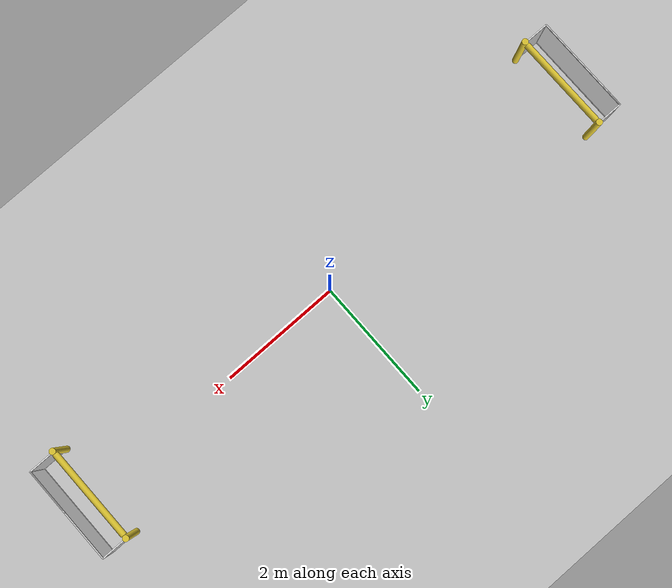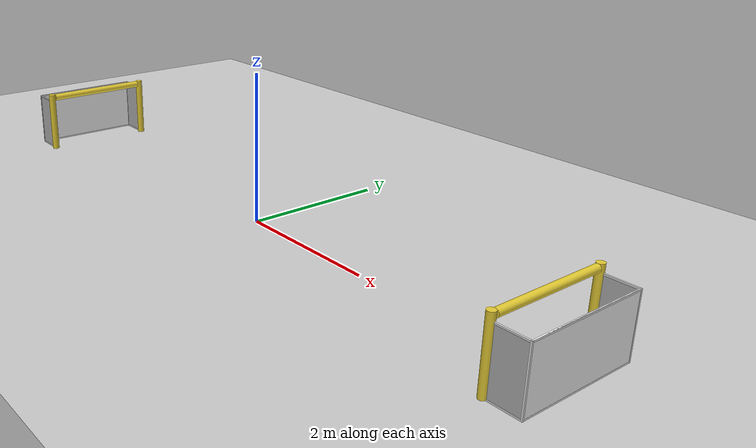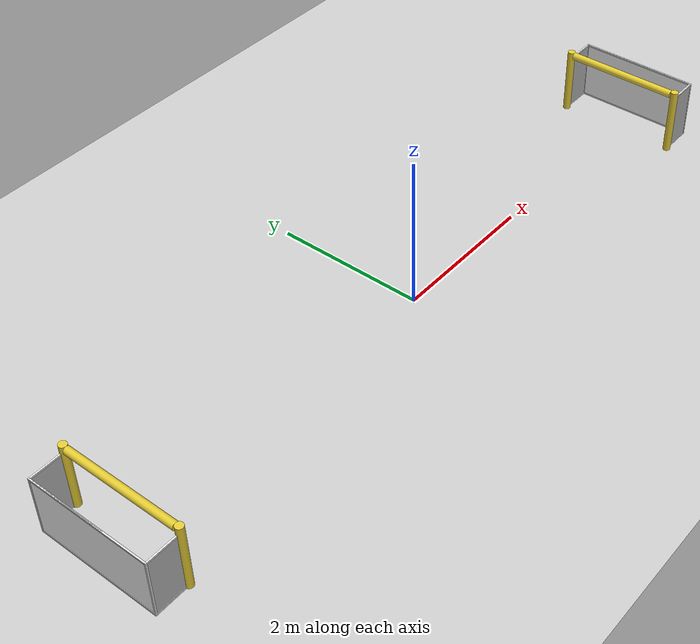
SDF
<sdf version="1.7">
 <world name="default">
  <light name="sun" type="directional">
   <pose>0 0 10 0 -0 0</pose>
   <diffuse>0.8 0.8 0.8 1</diffuse>
   <specular>0.2 0.2 0.2 1</specular>
   <attenuation>
    <range>1000</range>
    <constant>0.9</constant>
    <linear>0.01</linear>
    <quadratic>0.001</quadratic>
   </attenuation>
   <direction>-0.5 0.1 -0.9</direction>
   <spot><inner_angle>0</inner_angle><outer_angle>0</outer_angle><falloff>0</falloff></spot>
  </light>
  <model name="ground_plane">
   <static>1</static>
   <link name="link">
    <collision name="collision">
     <geometry><plane><normal>0 0 1</normal><size>100 100</size></plane></geometry>
     <surface><friction><ode><mu>100</mu><mu2>50</mu2></ode></friction></surface>
    </collision>
    <visual name="visual">
     <cast_shadows>0</cast_shadows>
     <geometry><plane><normal>0 0 1</normal><size>100 100</size></plane></geometry>
     <material>
      <script><uri>file://media/materials/scripts/gazebo.material</uri><name>Gazebo/Grey</name></script>
     </material>
    </visual>
   </link>
  </model>
  <gravity>0 0 -9.8</gravity>
  <magnetic_field>6e-06 2.3e-05 -4.2e-05</magnetic_field>
  <atmosphere type="adiabatic"/>
  <physics type="ode">
   <max_step_size>0.001</max_step_size>
   <real_time_factor>1</real_time_factor>
   <real_time_update_rate>1000</real_time_update_rate>
  </physics>
  <scene><ambient>0.4 0.4 0.4 1</ambient><background>0.7 0.7 0.7 1</background><shadows>1</shadows></scene>
  <spherical_coordinates>
   <surface_model>EARTH_WGS84</surface_model>
   <latitude_deg>0</latitude_deg>
   <longitude_deg>0</longitude_deg>
   <elevation>0</elevation>
   <heading_deg>0</heading_deg>
  </spherical_coordinates>
  <model name="WALLS">
   <link name="Wall_15">
    <pose>0 -3.78 0 0 -0 3.1397</pose>
    <inertial>
     <mass>1</mass>
     <inertia><ixx>1</ixx><ixy>0</ixy><ixz>0</ixz><iyy>1</iyy><iyz>0</iyz><izz>1</izz></inertia>
    </inertial>
    <visual name="Wall_15_Visual">
     <pose>0 0 2.5 0 -0 0</pose>
     <geometry><box><size>10.69 0.15 5</size></box></geometry>
     <material>
      <script><uri>file://media/materials/scripts/gazebo.material</uri><name>Gazebo/Grey</name></script>
      <ambient>1 1 1 1</ambient>
      <shader type="pixel"><normal_map>__default__</normal_map></shader>
      <diffuse>0.7 0.7 0.7 1</diffuse>
      <specular>0.01 0.01 0.01 1</specular>
      <emissive>0 0 0 1</emissive>
     </material>
     <meta><layer>0</layer></meta>
     <transparency>1</transparency>
    </visual>
    <collision name="Wall_15_Collision">
     <pose>0 0 2.5 0 -0 0</pose>
     <geometry><box><size>10.69 0.15 5</size></box></geometry>
     <surface>
      <friction>
       <ode><mu>1</mu><mu2>1</mu2><fdir1>0 0 0</fdir1><slip1>0</slip1><slip2>0</slip2></ode>
       <torsional>
        <coefficient>1</coefficient>
        <patch_radius>0</patch_radius>
        <surface_radius>0</surface_radius>
        <use_patch_radius>1</use_patch_radius>
        <ode><slip>0</slip></ode>
       </torsional>
      </friction>
      <bounce><restitution_coefficient>1</restitution_coefficient><threshold>1e+06</threshold></bounce>
      <contact>
       <collide_without_contact>0</collide_without_contact>
       <collide_without_contact_bitmask>1</collide_without_contact_bitmask>
       <collide_bitmask>1</collide_bitmask>
       <ode>
        <soft_cfm>0</soft_cfm>
        <soft_erp>0.2</soft_erp>
        <kp>1e+13</kp>
        <kd>1</kd>
        <max_vel>0.01</max_vel>
        <min_depth>0</min_depth>
       </ode>
       <bullet>
        <split_impulse>1</split_impulse>
        <split_impulse_penetration_threshold>-0.01</split_impulse_penetration_threshold>
        <soft_cfm>0</soft_cfm>
        <soft_erp>0.2</soft_erp>
        <kp>1e+13</kp>
        <kd>1</kd>
       </bullet>
      </contact>
     </surface>
    </collision>
   </link>
   <link name="Wall_18">
    <pose>0 3.78 0 0 0 -0.001898</pose>
    <inertial>
     <mass>1</mass>
     <inertia><ixx>1</ixx><ixy>0</ixy><ixz>0</ixz><iyy>1</iyy><iyz>0</iyz><izz>1</izz></inertia>
    </inertial>
    <visual name="Wall_18_Visual">
     <pose>0 0 2.5 0 -0 0</pose>
     <geometry><box><size>10.69 0.15 5</size></box></geometry>
     <material>
      <script><uri>file://media/materials/scripts/gazebo.material</uri><name>Gazebo/Grey</name></script>
      <ambient>1 1 1 1</ambient>
      <shader type="pixel"><normal_map>__default__</normal_map></shader>
      <diffuse>0.7 0.7 0.7 1</diffuse>
      <specular>0.01 0.01 0.01 1</specular>
      <emissive>0 0 0 1</emissive>
     </material>
     <meta><layer>0</layer></meta>
     <transparency>1</transparency>
    </visual>
    <collision name="Wall_18_Collision">
     <pose>0 0 2.5 0 -0 0</pose>
     <geometry><box><size>10.69 0.15 5</size></box></geometry>
     <surface>
      <friction>
       <ode><mu>1</mu><mu2>1</mu2><fdir1>0 0 0</fdir1><slip1>0</slip1><slip2>0</slip2></ode>
       <torsional>
        <coefficient>1</coefficient>
        <patch_radius>0</patch_radius>
        <surface_radius>0</surface_radius>
        <use_patch_radius>1</use_patch_radius>
        <ode><slip>0</slip></ode>
       </torsional>
      </friction>
      <bounce><restitution_coefficient>1</restitution_coefficient><threshold>1e+06</threshold></bounce>
      <contact>
       <collide_without_contact>0</collide_without_contact>
       <collide_without_contact_bitmask>1</collide_without_contact_bitmask>
       <collide_bitmask>1</collide_bitmask>
       <ode>
        <soft_cfm>0</soft_cfm>
        <soft_erp>0.2</soft_erp>
        <kp>1e+13</kp>
        <kd>1</kd>
        <max_vel>0.01</max_vel>
        <min_depth>0</min_depth>
       </ode>
       <bullet>
        <split_impulse>1</split_impulse>
        <split_impulse_penetration_threshold>-0.01</split_impulse_penetration_threshold>
        <soft_cfm>0</soft_cfm>
        <soft_erp>0.2</soft_erp>
        <kp>1e+13</kp>
        <kd>1</kd>
       </bullet>
      </contact>
     </surface>
    </collision>
   </link>
   <link name="Wall_20">
    <pose>-5.27 0.01 0 0 0 -1.5708</pose>
    <inertial>
     <mass>1</mass>
     <inertia><ixx>1</ixx><ixy>0</ixy><ixz>0</ixz><iyy>1</iyy><iyz>0</iyz><izz>1</izz></inertia>
    </inertial>
    <visual name="Wall_20_Visual">
     <pose>0 0 2.5 0 -0 0</pose>
     <geometry><box><size>7.71 0.15 5</size></box></geometry>
     <material>
      <script><uri>file://media/materials/scripts/gazebo.material</uri><name>Gazebo/Grey</name></script>
      <ambient>1 1 1 1</ambient>
      <shader type="pixel"><normal_map>__default__</normal_map></shader>
      <diffuse>0.7 0.7 0.7 1</diffuse>
      <specular>0.01 0.01 0.01 1</specular>
      <emissive>0 0 0 1</emissive>
     </material>
     <meta><layer>0</layer></meta>
     <transparency>1</transparency>
    </visual>
    <collision name="Wall_20_Collision">
     <pose>0 0 2.5 0 -0 0</pose>
     <geometry><box><size>7.71 0.15 5</size></box></geometry>
     <surface>
      <friction>
       <ode><mu>1</mu><mu2>1</mu2><fdir1>0 0 0</fdir1><slip1>0</slip1><slip2>0</slip2></ode>
       <torsional>
        <coefficient>1</coefficient>
        <patch_radius>0</patch_radius>
        <surface_radius>0</surface_radius>
        <use_patch_radius>1</use_patch_radius>
        <ode><slip>0</slip></ode>
       </torsional>
      </friction>
      <bounce><restitution_coefficient>1</restitution_coefficient><threshold>1e+06</threshold></bounce>
      <contact>
       <collide_without_contact>0</collide_without_contact>
       <collide_without_contact_bitmask>1</collide_without_contact_bitmask>
       <collide_bitmask>1</collide_bitmask>
       <ode>
        <soft_cfm>0</soft_cfm>
        <soft_erp>0.2</soft_erp>
        <kp>1e+13</kp>
        <kd>1</kd>
        <max_vel>0.01</max_vel>
        <min_depth>0</min_depth>
       </ode>
       <bullet>
        <split_impulse>1</split_impulse>
        <split_impulse_penetration_threshold>-0.01</split_impulse_penetration_threshold>
        <soft_cfm>0</soft_cfm>
        <soft_erp>0.2</soft_erp>
        <kp>1e+13</kp>
        <kd>1</kd>
       </bullet>
      </contact>
     </surface>
    </collision>
   </link>
   <link name="Wall_4">
    <pose>5.27 -0.01 0 0 -0 1.5708</pose>
    <inertial>
     <mass>1</mass>
     <inertia><ixx>1</ixx><ixy>0</ixy><ixz>0</ixz><iyy>1</iyy><iyz>0</iyz><izz>1</izz></inertia>
    </inertial>
    <visual name="Wall_4_Visual">
     <pose>0 0 2.5 0 -0 0</pose>
     <geometry><box><size>7.71 0.15 5</size></box></geometry>
     <material>
      <script><uri>file://media/materials/scripts/gazebo.material</uri><name>Gazebo/Grey</name></script>
      <ambient>1 1 1 1</ambient>
      <shader type="pixel"><normal_map>__default__</normal_map></shader>
      <diffuse>0.7 0.7 0.7 1</diffuse>
      <specular>0.01 0.01 0.01 1</specular>
      <emissive>0 0 0 1</emissive>
     </material>
     <meta><layer>0</layer></meta>
     <transparency>1</transparency>
    </visual>
    <collision name="Wall_4_Collision">
     <pose>0 0 2.5 0 -0 0</pose>
     <geometry><box><size>7.71 0.15 5</size></box></geometry>
     <surface>
      <friction>
       <ode><mu>1</mu><mu2>1</mu2><fdir1>0 0 0</fdir1><slip1>0</slip1><slip2>0</slip2></ode>
       <torsional>
        <coefficient>1</coefficient>
        <patch_radius>0</patch_radius>
        <surface_radius>0</surface_radius>
        <use_patch_radius>1</use_patch_radius>
        <ode><slip>0</slip></ode>
       </torsional>
      </friction>
      <bounce><restitution_coefficient>1</restitution_coefficient><threshold>1e+06</threshold></bounce>
      <contact>
       <collide_without_contact>0</collide_without_contact>
       <collide_without_contact_bitmask>1</collide_without_contact_bitmask>
       <collide_bitmask>1</collide_bitmask>
       <ode>
        <soft_cfm>0</soft_cfm>
        <soft_erp>0.2</soft_erp>
        <kp>1e+13</kp>
        <kd>1</kd>
        <max_vel>0.01</max_vel>
        <min_depth>0</min_depth>
       </ode>
       <bullet>
        <split_impulse>1</split_impulse>
        <split_impulse_penetration_threshold>-0.01</split_impulse_penetration_threshold>
        <soft_cfm>0</soft_cfm>
        <soft_erp>0.2</soft_erp>
        <kp>1e+13</kp>
        <kd>1</kd>
       </bullet>
      </contact>
     </surface>
    </collision>
   </link>
   <static>1</static>
   <pose>0 0.01 0 0 -0 0</pose>
  </model>
  <model name="WALLS2">
   <link name="Wall_13">
    <pose>-4.87158 0.88 0 0 -0 0</pose>
    <inertial>
     <mass>1</mass>
     <inertia><ixx>1</ixx><ixy>0</ixy><ixz>0</ixz><iyy>1</iyy><iyz>0</iyz><izz>1</izz></inertia>
    </inertial>
    <visual name="Wall_13_Visual">
     <pose>0 0 0.45 0 -0 0</pose>
     <geometry><box><size>0.65 0.15 0.9</size></box></geometry>
     <material>
      <script><uri>file://media/materials/scripts/gazebo.material</uri><name>Gazebo/Grey</name></script>
      <ambient>1 1 1 1</ambient>
      <shader type="pixel"><normal_map>__default__</normal_map></shader>
      <diffuse>0.7 0.7 0.7 1</diffuse>
      <specular>0.01 0.01 0.01 1</specular>
      <emissive>0 0 0 1</emissive>
     </material>
     <meta><layer>0</layer></meta>
     <transparency>1</transparency>
    </visual>
    <collision name="Wall_13_Collision">
     <pose>0 0 0.45 0 -0 0</pose>
     <geometry><box><size>0.65 0.15 0.9</size></box></geometry>
     <surface>
      <friction>
       <ode><mu>1</mu><mu2>1</mu2><fdir1>0 0 0</fdir1><slip1>0</slip1><slip2>0</slip2></ode>
       <torsional>
        <coefficient>1</coefficient>
        <patch_radius>0</patch_radius>
        <surface_radius>0</surface_radius>
        <use_patch_radius>1</use_patch_radius>
        <ode><slip>0</slip></ode>
       </torsional>
      </friction>
      <bounce><restitution_coefficient>0</restitution_coefficient><threshold>1e+06</threshold></bounce>
      <contact>
       <collide_without_contact>0</collide_without_contact>
       <collide_without_contact_bitmask>1</collide_without_contact_bitmask>
       <collide_bitmask>1</collide_bitmask>
       <ode>
        <soft_cfm>0</soft_cfm>
        <soft_erp>0.2</soft_erp>
        <kp>1e+13</kp>
        <kd>1</kd>
        <max_vel>0.01</max_vel>
        <min_depth>0</min_depth>
       </ode>
       <bullet>
        <split_impulse>1</split_impulse>
        <split_impulse_penetration_threshold>-0.01</split_impulse_penetration_threshold>
        <soft_cfm>0</soft_cfm>
        <soft_erp>0.2</soft_erp>
        <kp>1e+13</kp>
        <kd>1</kd>
       </bullet>
      </contact>
     </surface>
    </collision>
   </link>
   <link name="Wall_15">
    <pose>-4.87158 -0.88 0 0 -0 0</pose>
    <inertial>
     <mass>1</mass>
     <inertia><ixx>1</ixx><ixy>0</ixy><ixz>0</ixz><iyy>1</iyy><iyz>0</iyz><izz>1</izz></inertia>
    </inertial>
    <visual name="Wall_15_Visual">
     <pose>0 0 0.45 0 -0 0</pose>
     <geometry><box><size>0.65 0.15 0.9</size></box></geometry>
     <material>
      <script><uri>file://media/materials/scripts/gazebo.material</uri><name>Gazebo/Grey</name></script>
      <ambient>1 1 1 1</ambient>
      <shader type="pixel"><normal_map>__default__</normal_map></shader>
      <diffuse>0.7 0.7 0.7 1</diffuse>
      <specular>0.01 0.01 0.01 1</specular>
      <emissive>0 0 0 1</emissive>
     </material>
     <meta><layer>0</layer></meta>
     <transparency>1</transparency>
    </visual>
    <collision name="Wall_15_Collision">
     <pose>0 0 0.45 0 -0 0</pose>
     <geometry><box><size>0.65 0.15 0.9</size></box></geometry>
     <surface>
      <friction>
       <ode><mu>1</mu><mu2>1</mu2><fdir1>0 0 0</fdir1><slip1>0</slip1><slip2>0</slip2></ode>
       <torsional>
        <coefficient>1</coefficient>
        <patch_radius>0</patch_radius>
        <surface_radius>0</surface_radius>
        <use_patch_radius>1</use_patch_radius>
        <ode><slip>0</slip></ode>
       </torsional>
      </friction>
      <bounce><restitution_coefficient>0</restitution_coefficient><threshold>1e+06</threshold></bounce>
      <contact>
       <collide_without_contact>0</collide_without_contact>
       <collide_without_contact_bitmask>1</collide_without_contact_bitmask>
       <collide_bitmask>1</collide_bitmask>
       <ode>
        <soft_cfm>0</soft_cfm>
        <soft_erp>0.2</soft_erp>
        <kp>1e+13</kp>
        <kd>1</kd>
        <max_vel>0.01</max_vel>
        <min_depth>0</min_depth>
       </ode>
       <bullet>
        <split_impulse>1</split_impulse>
        <split_impulse_penetration_threshold>-0.01</split_impulse_penetration_threshold>
        <soft_cfm>0</soft_cfm>
        <soft_erp>0.2</soft_erp>
        <kp>1e+13</kp>
        <kd>1</kd>
       </bullet>
      </contact>
     </surface>
    </collision>
   </link>
   <link name="Wall_2">
    <pose>4.87141 -0.88 0 0 -0 0</pose>
    <inertial>
     <mass>1</mass>
     <inertia><ixx>1</ixx><ixy>0</ixy><ixz>0</ixz><iyy>1</iyy><iyz>0</iyz><izz>1</izz></inertia>
    </inertial>
    <visual name="Wall_2_Visual">
     <pose>0 0 0.45 0 -0 0</pose>
     <geometry><box><size>0.65 0.15 0.9</size></box></geometry>
     <material>
      <script><uri>file://media/materials/scripts/gazebo.material</uri><name>Gazebo/Grey</name></script>
      <ambient>1 1 1 1</ambient>
      <shader type="pixel"><normal_map>__default__</normal_map></shader>
      <diffuse>0.7 0.7 0.7 1</diffuse>
      <specular>0.01 0.01 0.01 1</specular>
      <emissive>0 0 0 1</emissive>
     </material>
     <meta><layer>0</layer></meta>
     <transparency>1</transparency>
    </visual>
    <collision name="Wall_2_Collision">
     <pose>0 0 0.45 0 -0 0</pose>
     <geometry><box><size>0.65 0.15 0.9</size></box></geometry>
     <surface>
      <friction>
       <ode><mu>1</mu><mu2>1</mu2><fdir1>0 0 0</fdir1><slip1>0</slip1><slip2>0</slip2></ode>
       <torsional>
        <coefficient>1</coefficient>
        <patch_radius>0</patch_radius>
        <surface_radius>0</surface_radius>
        <use_patch_radius>1</use_patch_radius>
        <ode><slip>0</slip></ode>
       </torsional>
      </friction>
      <bounce><restitution_coefficient>0</restitution_coefficient><threshold>1e+06</threshold></bounce>
      <contact>
       <collide_without_contact>0</collide_without_contact>
       <collide_without_contact_bitmask>1</collide_without_contact_bitmask>
       <collide_bitmask>1</collide_bitmask>
       <ode>
        <soft_cfm>0</soft_cfm>
        <soft_erp>0.2</soft_erp>
        <kp>1e+13</kp>
        <kd>1</kd>
        <max_vel>0.01</max_vel>
        <min_depth>0</min_depth>
       </ode>
       <bullet>
        <split_impulse>1</split_impulse>
        <split_impulse_penetration_threshold>-0.01</split_impulse_penetration_threshold>
        <soft_cfm>0</soft_cfm>
        <soft_erp>0.2</soft_erp>
        <kp>1e+13</kp>
        <kd>1</kd>
       </bullet>
      </contact>
     </surface>
    </collision>
   </link>
   <link name="Wall_20">
    <pose>-5.12158 0 0 0 0 -1.5708</pose>
    <inertial>
     <mass>1</mass>
     <inertia><ixx>1</ixx><ixy>0</ixy><ixz>0</ixz><iyy>1</iyy><iyz>0</iyz><izz>1</izz></inertia>
    </inertial>
    <visual name="Wall_20_Visual">
     <pose>0 0 0.45 0 -0 0</pose>
     <geometry><box><size>1.96 0.2 0.9</size></box></geometry>
     <material>
      <script><uri>file://media/materials/scripts/gazebo.material</uri><name>Gazebo/Grey</name></script>
      <ambient>1 1 1 1</ambient>
      <shader type="pixel"><normal_map>__default__</normal_map></shader>
      <diffuse>0.7 0.7 0.7 1</diffuse>
      <specular>0.01 0.01 0.01 1</specular>
      <emissive>0 0 0 1</emissive>
     </material>
     <meta><layer>0</layer></meta>
     <transparency>1</transparency>
    </visual>
    <collision name="Wall_20_Collision">
     <pose>0 0 0.45 0 -0 0</pose>
     <geometry><box><size>1.96 0.2 0.9</size></box></geometry>
     <surface>
      <friction>
       <ode><mu>1</mu><mu2>1</mu2><fdir1>0 0 0</fdir1><slip1>0</slip1><slip2>0</slip2></ode>
       <torsional>
        <coefficient>1</coefficient>
        <patch_radius>0</patch_radius>
        <surface_radius>0</surface_radius>
        <use_patch_radius>1</use_patch_radius>
        <ode><slip>0</slip></ode>
       </torsional>
      </friction>
      <bounce><restitution_coefficient>0</restitution_coefficient><threshold>1e+06</threshold></bounce>
      <contact>
       <collide_without_contact>0</collide_without_contact>
       <collide_without_contact_bitmask>1</collide_without_contact_bitmask>
       <collide_bitmask>1</collide_bitmask>
       <ode>
        <soft_cfm>0</soft_cfm>
        <soft_erp>0.2</soft_erp>
        <kp>1e+13</kp>
        <kd>1</kd>
        <max_vel>0.01</max_vel>
        <min_depth>0</min_depth>
       </ode>
       <bullet>
        <split_impulse>1</split_impulse>
        <split_impulse_penetration_threshold>-0.01</split_impulse_penetration_threshold>
        <soft_cfm>0</soft_cfm>
        <soft_erp>0.2</soft_erp>
        <kp>1e+13</kp>
        <kd>1</kd>
       </bullet>
      </contact>
     </surface>
    </collision>
   </link>
   <link name="Wall_5">
    <pose>5.11991 0 0 0 -0 1.5725</pose>
    <inertial>
     <mass>1</mass>
     <inertia><ixx>1</ixx><ixy>0</ixy><ixz>0</ixz><iyy>1</iyy><iyz>0</iyz><izz>1</izz></inertia>
    </inertial>
    <visual name="Wall_5_Visual">
     <pose>0 0 0.45 0 -0 0</pose>
     <geometry><box><size>1.96 0.2 0.9</size></box></geometry>
     <material>
      <script><uri>file://media/materials/scripts/gazebo.material</uri><name>Gazebo/Grey</name></script>
      <ambient>1 1 1 1</ambient>
      <shader type="pixel"><normal_map>__default__</normal_map></shader>
      <diffuse>0.7 0.7 0.7 1</diffuse>
      <specular>0.01 0.01 0.01 1</specular>
      <emissive>0 0 0 1</emissive>
     </material>
     <meta><layer>0</layer></meta>
     <transparency>1</transparency>
    </visual>
    <collision name="Wall_5_Collision">
     <pose>0 0 0.45 0 -0 0</pose>
     <geometry><box><size>1.96 0.2 0.9</size></box></geometry>
     <surface>
      <friction>
       <ode><mu>1</mu><mu2>1</mu2><fdir1>0 0 0</fdir1><slip1>0</slip1><slip2>0</slip2></ode>
       <torsional>
        <coefficient>1</coefficient>
        <patch_radius>0</patch_radius>
        <surface_radius>0</surface_radius>
        <use_patch_radius>1</use_patch_radius>
        <ode><slip>0</slip></ode>
       </torsional>
      </friction>
      <bounce><restitution_coefficient>0</restitution_coefficient><threshold>1e+06</threshold></bounce>
      <contact>
       <collide_without_contact>0</collide_without_contact>
       <collide_without_contact_bitmask>1</collide_without_contact_bitmask>
       <collide_bitmask>1</collide_bitmask>
       <ode>
        <soft_cfm>0</soft_cfm>
        <soft_erp>0.2</soft_erp>
        <kp>1e+13</kp>
        <kd>1</kd>
        <max_vel>0.01</max_vel>
        <min_depth>0</min_depth>
       </ode>
       <bullet>
        <split_impulse>1</split_impulse>
        <split_impulse_penetration_threshold>-0.01</split_impulse_penetration_threshold>
        <soft_cfm>0</soft_cfm>
        <soft_erp>0.2</soft_erp>
        <kp>1e+13</kp>
        <kd>1</kd>
       </bullet>
      </contact>
     </surface>
    </collision>
   </link>
   <link name="Wall_6">
    <pose>4.86841 0.88 0 0 -0 3.14159</pose>
    <inertial>
     <mass>1</mass>
     <inertia><ixx>1</ixx><ixy>0</ixy><ixz>0</ixz><iyy>1</iyy><iyz>0</iyz><izz>1</izz></inertia>
    </inertial>
    <visual name="Wall_6_Visual">
     <pose>0 0 0.45 0 -0 0</pose>
     <geometry><box><size>0.65 0.15 0.9</size></box></geometry>
     <material>
      <script><uri>file://media/materials/scripts/gazebo.material</uri><name>Gazebo/Grey</name></script>
      <ambient>1 1 1 1</ambient>
      <shader type="pixel"><normal_map>__default__</normal_map></shader>
      <diffuse>0.7 0.7 0.7 1</diffuse>
      <specular>0.01 0.01 0.01 1</specular>
      <emissive>0 0 0 1</emissive>
     </material>
     <meta><layer>0</layer></meta>
     <transparency>1</transparency>
    </visual>
    <collision name="Wall_6_Collision">
     <pose>0 0 0.45 0 -0 0</pose>
     <geometry><box><size>0.65 0.15 0.9</size></box></geometry>
     <surface>
      <friction>
       <ode><mu>1</mu><mu2>1</mu2><fdir1>0 0 0</fdir1><slip1>0</slip1><slip2>0</slip2></ode>
       <torsional>
        <coefficient>1</coefficient>
        <patch_radius>0</patch_radius>
        <surface_radius>0</surface_radius>
        <use_patch_radius>1</use_patch_radius>
        <ode><slip>0</slip></ode>
       </torsional>
      </friction>
      <bounce><restitution_coefficient>0</restitution_coefficient><threshold>1e+06</threshold></bounce>
      <contact>
       <collide_without_contact>0</collide_without_contact>
       <collide_without_contact_bitmask>1</collide_without_contact_bitmask>
       <collide_bitmask>1</collide_bitmask>
       <ode>
        <soft_cfm>0</soft_cfm>
        <soft_erp>0.2</soft_erp>
        <kp>1e+13</kp>
        <kd>1</kd>
        <max_vel>0.01</max_vel>
        <min_depth>0</min_depth>
       </ode>
       <bullet>
        <split_impulse>1</split_impulse>
        <split_impulse_penetration_threshold>-0.01</split_impulse_penetration_threshold>
        <soft_cfm>0</soft_cfm>
        <soft_erp>0.2</soft_erp>
        <kp>1e+13</kp>
        <kd>1</kd>
       </bullet>
      </contact>
     </surface>
    </collision>
   </link>
   <static>1</static>
   <pose>0.00158 0 0 0 -0 0</pose>
  </model>
  <model name="RoboCup_2014_SPL_Goal_clone">
   <link name="left_post">
    <pose>0 0.8 0.45 0 -0 0</pose>
    <inertial>
     <mass>1</mass>
     <inertia><ixx>1</ixx><ixy>0</ixy><ixz>0</ixz><iyy>1</iyy><iyz>0</iyz><izz>1</izz></inertia>
    </inertial>
    <visual name="visual">
     <geometry><cylinder><radius>0.05</radius><length>0.9</length></cylinder></geometry>
     <material>
      <script><uri>file://media/materials/scripts/gazebo.material</uri><name>Gazebo/ZincYellow</name></script>
      <shader type="pixel"><normal_map>__default__</normal_map></shader>
     </material>
    </visual>
    <collision name="collision">
     <geometry><cylinder><radius>0.05</radius><length>0.9</length></cylinder></geometry>
     <surface>
      <friction>
       <ode><mu>1</mu><mu2>1</mu2><fdir1>0 0 0</fdir1><slip1>0</slip1><slip2>0</slip2></ode>
       <torsional>
        <coefficient>1</coefficient>
        <patch_radius>0</patch_radius>
        <surface_radius>0</surface_radius>
        <use_patch_radius>1</use_patch_radius>
        <ode><slip>0</slip></ode>
       </torsional>
      </friction>
      <bounce><restitution_coefficient>1</restitution_coefficient><threshold>1e+06</threshold></bounce>
      <contact>
       <collide_without_contact>0</collide_without_contact>
       <collide_without_contact_bitmask>1</collide_without_contact_bitmask>
       <collide_bitmask>1</collide_bitmask>
       <ode>
        <soft_cfm>0</soft_cfm>
        <soft_erp>0.2</soft_erp>
        <kp>1e+13</kp>
        <kd>1</kd>
        <max_vel>0.01</max_vel>
        <min_depth>0</min_depth>
       </ode>
       <bullet>
        <split_impulse>1</split_impulse>
        <split_impulse_penetration_threshold>-0.01</split_impulse_penetration_threshold>
        <soft_cfm>0</soft_cfm>
        <soft_erp>0.2</soft_erp>
        <kp>1e+13</kp>
        <kd>1</kd>
       </bullet>
      </contact>
     </surface>
    </collision>
   </link>
   <link name="center_net">
    <pose>0.44 0 0.4 0 -0 0</pose>
    <inertial>
     <mass>1</mass>
     <inertia><ixx>1</ixx><ixy>0</ixy><ixz>0</ixz><iyy>1</iyy><iyz>0</iyz><izz>1</izz></inertia>
    </inertial>
    <visual name="visual">
     <geometry><box><size>0.01 1.6 0.8</size></box></geometry>
     <material>
      <script>
       <uri>model://robocup09_spl_field/materials/scripts/</uri>
       <uri>model://robocup09_spl_field/materials/textures/</uri>
       <name>RoboCup/Net</name>
      </script>
      <shader type="pixel"><normal_map>__default__</normal_map></shader>
      <ambient>1 1 1 1</ambient>
      <diffuse>1 1 1 1</diffuse>
      <specular>0 0 0 1</specular>
      <emissive>0 0 0 1</emissive>
     </material>
    </visual>
    <collision name="collision">
     <geometry><box><size>0.01 1.6 0.8</size></box></geometry>
     <surface>
      <friction>
       <ode><mu>1</mu><mu2>1</mu2><fdir1>0 0 0</fdir1><slip1>0</slip1><slip2>0</slip2></ode>
       <torsional>
        <coefficient>1</coefficient>
        <patch_radius>0</patch_radius>
        <surface_radius>0</surface_radius>
        <use_patch_radius>1</use_patch_radius>
        <ode><slip>0</slip></ode>
       </torsional>
      </friction>
      <bounce><restitution_coefficient>0</restitution_coefficient><threshold>1e+06</threshold></bounce>
      <contact>
       <collide_without_contact>0</collide_without_contact>
       <collide_without_contact_bitmask>1</collide_without_contact_bitmask>
       <collide_bitmask>1</collide_bitmask>
       <ode>
        <soft_cfm>0</soft_cfm>
        <soft_erp>0.2</soft_erp>
        <kp>1e+13</kp>
        <kd>1</kd>
        <max_vel>0.01</max_vel>
        <min_depth>0</min_depth>
       </ode>
       <bullet>
        <split_impulse>1</split_impulse>
        <split_impulse_penetration_threshold>-0.01</split_impulse_penetration_threshold>
        <soft_cfm>0</soft_cfm>
        <soft_erp>0.2</soft_erp>
        <kp>1e+13</kp>
        <kd>1</kd>
       </bullet>
      </contact>
     </surface>
    </collision>
   </link>
   <link name="center_support_horiz_lower">
    <pose>0.44 0 0.01 3.14159 1.57079 3.14159</pose>
    <visual name="visual">
     <geometry><box><size>0.02 1.58 0.02</size></box></geometry>
     <material>
      <script><uri>file://media/materials/scripts/gazebo.material</uri><name>Gazebo/White</name></script>
      <shader type="pixel"/>
     </material>
    </visual>
    <collision name="collision">
     <geometry><box><size>0.02 1.58 0.02</size></box></geometry>
     <surface>
      <friction>
       <ode><mu>1</mu><mu2>1</mu2><fdir1>0 0 0</fdir1><slip1>0</slip1><slip2>0</slip2></ode>
       <torsional>
        <coefficient>1</coefficient>
        <patch_radius>0</patch_radius>
        <surface_radius>0</surface_radius>
        <use_patch_radius>1</use_patch_radius>
        <ode><slip>0</slip></ode>
       </torsional>
      </friction>
      <bounce><restitution_coefficient>0</restitution_coefficient><threshold>1e+06</threshold></bounce>
      <contact>
       <collide_without_contact>0</collide_without_contact>
       <collide_without_contact_bitmask>1</collide_without_contact_bitmask>
       <collide_bitmask>1</collide_bitmask>
       <ode>
        <soft_cfm>0</soft_cfm>
        <soft_erp>0.2</soft_erp>
        <kp>1e+13</kp>
        <kd>1</kd>
        <max_vel>0.01</max_vel>
        <min_depth>0</min_depth>
       </ode>
       <bullet>
        <split_impulse>1</split_impulse>
        <split_impulse_penetration_threshold>-0.01</split_impulse_penetration_threshold>
        <soft_cfm>0</soft_cfm>
        <soft_erp>0.2</soft_erp>
        <kp>1e+13</kp>
        <kd>1</kd>
       </bullet>
      </contact>
     </surface>
    </collision>
   </link>
   <link name="center_support_horiz_upper">
    <pose>0.44 0 0.79 3.14159 1.57079 3.14159</pose>
    <visual name="visual">
     <geometry><box><size>0.02 1.58 0.02</size></box></geometry>
     <material>
      <script><uri>file://media/materials/scripts/gazebo.material</uri><name>Gazebo/White</name></script>
      <shader type="pixel"/>
     </material>
    </visual>
    <collision name="collision">
     <geometry><box><size>0.02 1.58 0.02</size></box></geometry>
     <surface>
      <friction>
       <ode><mu>1</mu><mu2>1</mu2><fdir1>0 0 0</fdir1><slip1>0</slip1><slip2>0</slip2></ode>
       <torsional>
        <coefficient>1</coefficient>
        <patch_radius>0</patch_radius>
        <surface_radius>0</surface_radius>
        <use_patch_radius>1</use_patch_radius>
        <ode><slip>0</slip></ode>
       </torsional>
      </friction>
      <bounce><restitution_coefficient>0</restitution_coefficient><threshold>1e+06</threshold></bounce>
      <contact>
       <collide_without_contact>0</collide_without_contact>
       <collide_without_contact_bitmask>1</collide_without_contact_bitmask>
       <collide_bitmask>1</collide_bitmask>
       <ode>
        <soft_cfm>0</soft_cfm>
        <soft_erp>0.2</soft_erp>
        <kp>1e+13</kp>
        <kd>1</kd>
        <max_vel>0.01</max_vel>
        <min_depth>0</min_depth>
       </ode>
       <bullet>
        <split_impulse>1</split_impulse>
        <split_impulse_penetration_threshold>-0.01</split_impulse_penetration_threshold>
        <soft_cfm>0</soft_cfm>
        <soft_erp>0.2</soft_erp>
        <kp>1e+13</kp>
        <kd>1</kd>
       </bullet>
      </contact>
     </surface>
    </collision>
   </link>
   <link name="crossbar">
    <pose>0 0 0.85 1.56994 1.57 -4.3e-05</pose>
    <inertial>
     <mass>1</mass>
     <inertia><ixx>1</ixx><ixy>0</ixy><ixz>0</ixz><iyy>1</iyy><iyz>0</iyz><izz>1</izz></inertia>
    </inertial>
    <visual name="visual">
     <geometry><cylinder><radius>0.05</radius><length>1.5</length></cylinder></geometry>
     <material>
      <script><uri>file://media/materials/scripts/gazebo.material</uri><name>Gazebo/ZincYellow</name></script>
      <shader type="pixel"><normal_map>__default__</normal_map></shader>
      <ambient>0.973 0.953 0.208 1</ambient>
      <diffuse>0.973 0.953 0.208 1</diffuse>
      <specular>0.973 0.953 0.208 1</specular>
      <emissive>0 0 0 1</emissive>
     </material>
    </visual>
    <collision name="collision">
     <geometry><cylinder><radius>0.05</radius><length>1.5</length></cylinder></geometry>
     <surface>
      <friction>
       <ode><mu>1</mu><mu2>1</mu2><fdir1>0 0 0</fdir1><slip1>0</slip1><slip2>0</slip2></ode>
       <torsional>
        <coefficient>1</coefficient>
        <patch_radius>0</patch_radius>
        <surface_radius>0</surface_radius>
        <use_patch_radius>1</use_patch_radius>
        <ode><slip>0</slip></ode>
       </torsional>
      </friction>
      <bounce><restitution_coefficient>1</restitution_coefficient><threshold>1e+06</threshold></bounce>
      <contact>
       <collide_without_contact>0</collide_without_contact>
       <collide_without_contact_bitmask>1</collide_without_contact_bitmask>
       <collide_bitmask>1</collide_bitmask>
       <ode>
        <soft_cfm>0</soft_cfm>
        <soft_erp>0.2</soft_erp>
        <kp>1e+13</kp>
        <kd>1</kd>
        <max_vel>0.01</max_vel>
        <min_depth>0</min_depth>
       </ode>
       <bullet>
        <split_impulse>1</split_impulse>
        <split_impulse_penetration_threshold>-0.01</split_impulse_penetration_threshold>
        <soft_cfm>0</soft_cfm>
        <soft_erp>0.2</soft_erp>
        <kp>1e+13</kp>
        <kd>1</kd>
       </bullet>
      </contact>
     </surface>
    </collision>
    <collision name="collision_1">
     <pose>0.05 0.3 0 0 -0 0</pose>
     <geometry><box><size>0.05 0.5 1.6</size></box></geometry>
     <surface>
      <friction>
       <ode><mu>1</mu><mu2>1</mu2><fdir1>0 0 0</fdir1><slip1>0</slip1><slip2>0</slip2></ode>
       <torsional>
        <coefficient>1</coefficient>
        <patch_radius>0</patch_radius>
        <surface_radius>0</surface_radius>
        <use_patch_radius>1</use_patch_radius>
        <ode><slip>0</slip></ode>
       </torsional>
      </friction>
      <bounce><restitution_coefficient>1</restitution_coefficient><threshold>1e+06</threshold></bounce>
      <contact>
       <collide_without_contact>0</collide_without_contact>
       <collide_without_contact_bitmask>1</collide_without_contact_bitmask>
       <collide_bitmask>1</collide_bitmask>
       <ode>
        <soft_cfm>0</soft_cfm>
        <soft_erp>0.2</soft_erp>
        <kp>1e+13</kp>
        <kd>1</kd>
        <max_vel>0.01</max_vel>
        <min_depth>0</min_depth>
       </ode>
       <bullet>
        <split_impulse>1</split_impulse>
        <split_impulse_penetration_threshold>-0.01</split_impulse_penetration_threshold>
        <soft_cfm>0</soft_cfm>
        <soft_erp>0.2</soft_erp>
        <kp>1e+13</kp>
        <kd>1</kd>
       </bullet>
      </contact>
     </surface>
    </collision>
   </link>
   <link name="left_net">
    <pose>0.24 0.8 0.4 0 -0 0</pose>
    <visual name="visual">
     <geometry><box><size>0.38 0.01 0.76</size></box></geometry>
     <material>
      <script>
       <uri>model://robocup09_spl_field/materials/scripts/</uri>
       <uri>model://robocup09_spl_field/materials/textures/</uri>
       <name>RoboCup/Net</name>
      </script>
      <shader type="pixel"/>
     </material>
    </visual>
    <collision name="collision">
     <geometry><box><size>0.38 0.01 0.76</size></box></geometry>
     <surface>
      <friction>
       <ode><mu>1</mu><mu2>1</mu2><fdir1>0 0 0</fdir1><slip1>0</slip1><slip2>0</slip2></ode>
       <torsional>
        <coefficient>1</coefficient>
        <patch_radius>0</patch_radius>
        <surface_radius>0</surface_radius>
        <use_patch_radius>1</use_patch_radius>
        <ode><slip>0</slip></ode>
       </torsional>
      </friction>
      <bounce><restitution_coefficient>0</restitution_coefficient><threshold>1e+06</threshold></bounce>
      <contact>
       <collide_without_contact>0</collide_without_contact>
       <collide_without_contact_bitmask>1</collide_without_contact_bitmask>
       <collide_bitmask>1</collide_bitmask>
       <ode>
        <soft_cfm>0</soft_cfm>
        <soft_erp>0.2</soft_erp>
        <kp>1e+13</kp>
        <kd>1</kd>
        <max_vel>0.01</max_vel>
        <min_depth>0</min_depth>
       </ode>
       <bullet>
        <split_impulse>1</split_impulse>
        <split_impulse_penetration_threshold>-0.01</split_impulse_penetration_threshold>
        <soft_cfm>0</soft_cfm>
        <soft_erp>0.2</soft_erp>
        <kp>1e+13</kp>
        <kd>1</kd>
       </bullet>
      </contact>
     </surface>
    </collision>
   </link>
   <link name="left_support_horiz_lower">
    <pose>0.24 0.8 0.01 0 -0 0</pose>
    <visual name="visual">
     <geometry><box><size>0.38 0.02 0.02</size></box></geometry>
     <material>
      <script><uri>file://media/materials/scripts/gazebo.material</uri><name>Gazebo/White</name></script>
      <shader type="pixel"/>
     </material>
    </visual>
    <collision name="collision">
     <geometry><box><size>0.38 0.02 0.02</size></box></geometry>
     <surface>
      <friction>
       <ode><mu>1</mu><mu2>1</mu2><fdir1>0 0 0</fdir1><slip1>0</slip1><slip2>0</slip2></ode>
       <torsional>
        <coefficient>1</coefficient>
        <patch_radius>0</patch_radius>
        <surface_radius>0</surface_radius>
        <use_patch_radius>1</use_patch_radius>
        <ode><slip>0</slip></ode>
       </torsional>
      </friction>
      <bounce><restitution_coefficient>0</restitution_coefficient><threshold>1e+06</threshold></bounce>
      <contact>
       <collide_without_contact>0</collide_without_contact>
       <collide_without_contact_bitmask>1</collide_without_contact_bitmask>
       <collide_bitmask>1</collide_bitmask>
       <ode>
        <soft_cfm>0</soft_cfm>
        <soft_erp>0.2</soft_erp>
        <kp>1e+13</kp>
        <kd>1</kd>
        <max_vel>0.01</max_vel>
        <min_depth>0</min_depth>
       </ode>
       <bullet>
        <split_impulse>1</split_impulse>
        <split_impulse_penetration_threshold>-0.01</split_impulse_penetration_threshold>
        <soft_cfm>0</soft_cfm>
        <soft_erp>0.2</soft_erp>
        <kp>1e+13</kp>
        <kd>1</kd>
       </bullet>
      </contact>
     </surface>
    </collision>
   </link>
   <link name="left_support_horiz_upper">
    <pose>0.24 0.8 0.79 0 -0 0</pose>
    <visual name="visual">
     <geometry><box><size>0.38 0.02 0.02</size></box></geometry>
     <material>
      <script><uri>file://media/materials/scripts/gazebo.material</uri><name>Gazebo/White</name></script>
      <shader type="pixel"/>
     </material>
    </visual>
    <collision name="collision">
     <geometry><box><size>0.38 0.02 0.02</size></box></geometry>
     <surface>
      <friction>
       <ode><mu>1</mu><mu2>1</mu2><fdir1>0 0 0</fdir1><slip1>0</slip1><slip2>0</slip2></ode>
       <torsional>
        <coefficient>1</coefficient>
        <patch_radius>0</patch_radius>
        <surface_radius>0</surface_radius>
        <use_patch_radius>1</use_patch_radius>
        <ode><slip>0</slip></ode>
       </torsional>
      </friction>
      <bounce><restitution_coefficient>0</restitution_coefficient><threshold>1e+06</threshold></bounce>
      <contact>
       <collide_without_contact>0</collide_without_contact>
       <collide_without_contact_bitmask>1</collide_without_contact_bitmask>
       <collide_bitmask>1</collide_bitmask>
       <ode>
        <soft_cfm>0</soft_cfm>
        <soft_erp>0.2</soft_erp>
        <kp>1e+13</kp>
        <kd>1</kd>
        <max_vel>0.01</max_vel>
        <min_depth>0</min_depth>
       </ode>
       <bullet>
        <split_impulse>1</split_impulse>
        <split_impulse_penetration_threshold>-0.01</split_impulse_penetration_threshold>
        <soft_cfm>0</soft_cfm>
        <soft_erp>0.2</soft_erp>
        <kp>1e+13</kp>
        <kd>1</kd>
       </bullet>
      </contact>
     </surface>
    </collision>
   </link>
   <link name="left_support_vertical">
    <pose>0.44 0.8 0.4 3.14159 1.57079 3.14159</pose>
    <visual name="visual">
     <geometry><box><size>0.8 0.02 0.02</size></box></geometry>
     <material>
      <script><uri>file://media/materials/scripts/gazebo.material</uri><name>Gazebo/White</name></script>
      <shader type="pixel"/>
     </material>
    </visual>
    <collision name="collision">
     <geometry><box><size>0.8 0.02 0.02</size></box></geometry>
     <surface>
      <friction>
       <ode><mu>1</mu><mu2>1</mu2><fdir1>0 0 0</fdir1><slip1>0</slip1><slip2>0</slip2></ode>
       <torsional>
        <coefficient>1</coefficient>
        <patch_radius>0</patch_radius>
        <surface_radius>0</surface_radius>
        <use_patch_radius>1</use_patch_radius>
        <ode><slip>0</slip></ode>
       </torsional>
      </friction>
      <bounce><restitution_coefficient>0</restitution_coefficient><threshold>1e+06</threshold></bounce>
      <contact>
       <collide_without_contact>0</collide_without_contact>
       <collide_without_contact_bitmask>1</collide_without_contact_bitmask>
       <collide_bitmask>1</collide_bitmask>
       <ode>
        <soft_cfm>0</soft_cfm>
        <soft_erp>0.2</soft_erp>
        <kp>1e+13</kp>
        <kd>1</kd>
        <max_vel>0.01</max_vel>
        <min_depth>0</min_depth>
       </ode>
       <bullet>
        <split_impulse>1</split_impulse>
        <split_impulse_penetration_threshold>-0.01</split_impulse_penetration_threshold>
        <soft_cfm>0</soft_cfm>
        <soft_erp>0.2</soft_erp>
        <kp>1e+13</kp>
        <kd>1</kd>
       </bullet>
      </contact>
     </surface>
    </collision>
   </link>
   <link name="right_net">
    <pose>0.24 -0.8 0.4 0 -0 0</pose>
    <visual name="visual">
     <geometry><box><size>0.38 0.01 0.76</size></box></geometry>
     <material>
      <script>
       <uri>model://robocup09_spl_field/materials/scripts/</uri>
       <uri>model://robocup09_spl_field/materials/textures/</uri>
       <name>RoboCup/Net</name>
      </script>
      <shader type="pixel"/>
     </material>
    </visual>
    <collision name="collision">
     <geometry><box><size>0.38 0.01 0.76</size></box></geometry>
     <surface>
      <friction>
       <ode><mu>1</mu><mu2>1</mu2><fdir1>0 0 0</fdir1><slip1>0</slip1><slip2>0</slip2></ode>
       <torsional>
        <coefficient>1</coefficient>
        <patch_radius>0</patch_radius>
        <surface_radius>0</surface_radius>
        <use_patch_radius>1</use_patch_radius>
        <ode><slip>0</slip></ode>
       </torsional>
      </friction>
      <bounce><restitution_coefficient>0</restitution_coefficient><threshold>1e+06</threshold></bounce>
      <contact>
       <collide_without_contact>0</collide_without_contact>
       <collide_without_contact_bitmask>1</collide_without_contact_bitmask>
       <collide_bitmask>1</collide_bitmask>
       <ode>
        <soft_cfm>0</soft_cfm>
        <soft_erp>0.2</soft_erp>
        <kp>1e+13</kp>
        <kd>1</kd>
        <max_vel>0.01</max_vel>
        <min_depth>0</min_depth>
       </ode>
       <bullet>
        <split_impulse>1</split_impulse>
        <split_impulse_penetration_threshold>-0.01</split_impulse_penetration_threshold>
        <soft_cfm>0</soft_cfm>
        <soft_erp>0.2</soft_erp>
        <kp>1e+13</kp>
        <kd>1</kd>
       </bullet>
      </contact>
     </surface>
    </collision>
   </link>
   <link name="right_post">
    <pose>0 -0.8 0.45 0 -0 0</pose>
    <inertial>
     <mass>1</mass>
     <inertia><ixx>1</ixx><ixy>0</ixy><ixz>0</ixz><iyy>1</iyy><iyz>0</iyz><izz>1</izz></inertia>
    </inertial>
    <visual name="visual">
     <geometry><cylinder><radius>0.05</radius><length>0.9</length></cylinder></geometry>
     <material>
      <script><uri>file://media/materials/scripts/gazebo.material</uri><name>Gazebo/ZincYellow</name></script>
      <shader type="pixel"><normal_map>__default__</normal_map></shader>
     </material>
    </visual>
    <collision name="collision">
     <geometry><cylinder><radius>0.05</radius><length>0.9</length></cylinder></geometry>
     <surface>
      <friction>
       <ode><mu>1</mu><mu2>1</mu2><fdir1>0 0 0</fdir1><slip1>0</slip1><slip2>0</slip2></ode>
       <torsional>
        <coefficient>1</coefficient>
        <patch_radius>0</patch_radius>
        <surface_radius>0</surface_radius>
        <use_patch_radius>1</use_patch_radius>
        <ode><slip>0</slip></ode>
       </torsional>
      </friction>
      <bounce><restitution_coefficient>1</restitution_coefficient><threshold>1e+06</threshold></bounce>
      <contact>
       <collide_without_contact>0</collide_without_contact>
       <collide_without_contact_bitmask>1</collide_without_contact_bitmask>
       <collide_bitmask>1</collide_bitmask>
       <ode>
        <soft_cfm>0</soft_cfm>
        <soft_erp>0.2</soft_erp>
        <kp>1e+13</kp>
        <kd>1</kd>
        <max_vel>0.01</max_vel>
        <min_depth>0</min_depth>
       </ode>
       <bullet>
        <split_impulse>1</split_impulse>
        <split_impulse_penetration_threshold>-0.01</split_impulse_penetration_threshold>
        <soft_cfm>0</soft_cfm>
        <soft_erp>0.2</soft_erp>
        <kp>1e+13</kp>
        <kd>1</kd>
       </bullet>
      </contact>
     </surface>
    </collision>
   </link>
   <link name="right_support_horiz_lower">
    <pose>0.24 -0.8 0.01 0 -0 0</pose>
    <visual name="visual">
     <geometry><box><size>0.38 0.02 0.02</size></box></geometry>
     <material>
      <script><uri>file://media/materials/scripts/gazebo.material</uri><name>Gazebo/White</name></script>
      <shader type="pixel"/>
     </material>
    </visual>
    <collision name="collision">
     <geometry><box><size>0.38 0.02 0.02</size></box></geometry>
     <surface>
      <friction>
       <ode><mu>1</mu><mu2>1</mu2><fdir1>0 0 0</fdir1><slip1>0</slip1><slip2>0</slip2></ode>
       <torsional>
        <coefficient>1</coefficient>
        <patch_radius>0</patch_radius>
        <surface_radius>0</surface_radius>
        <use_patch_radius>1</use_patch_radius>
        <ode><slip>0</slip></ode>
       </torsional>
      </friction>
      <bounce><restitution_coefficient>0</restitution_coefficient><threshold>1e+06</threshold></bounce>
      <contact>
       <collide_without_contact>0</collide_without_contact>
       <collide_without_contact_bitmask>1</collide_without_contact_bitmask>
       <collide_bitmask>1</collide_bitmask>
       <ode>
        <soft_cfm>0</soft_cfm>
        <soft_erp>0.2</soft_erp>
        <kp>1e+13</kp>
        <kd>1</kd>
        <max_vel>0.01</max_vel>
        <min_depth>0</min_depth>
       </ode>
       <bullet>
        <split_impulse>1</split_impulse>
        <split_impulse_penetration_threshold>-0.01</split_impulse_penetration_threshold>
        <soft_cfm>0</soft_cfm>
        <soft_erp>0.2</soft_erp>
        <kp>1e+13</kp>
        <kd>1</kd>
       </bullet>
      </contact>
     </surface>
    </collision>
   </link>
   <link name="right_support_horiz_upper">
    <pose>0.24 -0.8 0.79 0 -0 0</pose>
    <visual name="visual">
     <geometry><box><size>0.38 0.02 0.02</size></box></geometry>
     <material>
      <script><uri>file://media/materials/scripts/gazebo.material</uri><name>Gazebo/White</name></script>
      <shader type="pixel"/>
     </material>
    </visual>
    <collision name="collision">
     <geometry><box><size>0.38 0.02 0.02</size></box></geometry>
     <surface>
      <friction>
       <ode><mu>1</mu><mu2>1</mu2><fdir1>0 0 0</fdir1><slip1>0</slip1><slip2>0</slip2></ode>
       <torsional>
        <coefficient>1</coefficient>
        <patch_radius>0</patch_radius>
        <surface_radius>0</surface_radius>
        <use_patch_radius>1</use_patch_radius>
        <ode><slip>0</slip></ode>
       </torsional>
      </friction>
      <bounce><restitution_coefficient>0</restitution_coefficient><threshold>1e+06</threshold></bounce>
      <contact>
       <collide_without_contact>0</collide_without_contact>
       <collide_without_contact_bitmask>1</collide_without_contact_bitmask>
       <collide_bitmask>1</collide_bitmask>
       <ode>
        <soft_cfm>0</soft_cfm>
        <soft_erp>0.2</soft_erp>
        <kp>1e+13</kp>
        <kd>1</kd>
        <max_vel>0.01</max_vel>
        <min_depth>0</min_depth>
       </ode>
       <bullet>
        <split_impulse>1</split_impulse>
        <split_impulse_penetration_threshold>-0.01</split_impulse_penetration_threshold>
        <soft_cfm>0</soft_cfm>
        <soft_erp>0.2</soft_erp>
        <kp>1e+13</kp>
        <kd>1</kd>
       </bullet>
      </contact>
     </surface>
    </collision>
   </link>
   <link name="right_support_vertical">
    <pose>0.44 -0.8 0.4 3.14159 1.57079 3.14159</pose>
    <visual name="visual">
     <geometry><box><size>0.8 0.02 0.02</size></box></geometry>
     <material>
      <script><uri>file://media/materials/scripts/gazebo.material</uri><name>Gazebo/White</name></script>
      <shader type="pixel"/>
     </material>
    </visual>
    <collision name="collision">
     <geometry><box><size>0.8 0.02 0.02</size></box></geometry>
     <surface>
      <friction>
       <ode><mu>1</mu><mu2>1</mu2><fdir1>0 0 0</fdir1><slip1>0</slip1><slip2>0</slip2></ode>
       <torsional>
        <coefficient>1</coefficient>
        <patch_radius>0</patch_radius>
        <surface_radius>0</surface_radius>
        <use_patch_radius>1</use_patch_radius>
        <ode><slip>0</slip></ode>
       </torsional>
      </friction>
      <bounce><restitution_coefficient>0</restitution_coefficient><threshold>1e+06</threshold></bounce>
      <contact>
       <collide_without_contact>0</collide_without_contact>
       <collide_without_contact_bitmask>1</collide_without_contact_bitmask>
       <collide_bitmask>1</collide_bitmask>
       <ode>
        <soft_cfm>0</soft_cfm>
        <soft_erp>0.2</soft_erp>
        <kp>1e+13</kp>
        <kd>1</kd>
        <max_vel>0.01</max_vel>
        <min_depth>0</min_depth>
       </ode>
       <bullet>
        <split_impulse>1</split_impulse>
        <split_impulse_penetration_threshold>-0.01</split_impulse_penetration_threshold>
        <soft_cfm>0</soft_cfm>
        <soft_erp>0.2</soft_erp>
        <kp>1e+13</kp>
        <kd>1</kd>
       </bullet>
      </contact>
     </surface>
    </collision>
   </link>
   <static>1</static>
   <pose>4.5 0 0 0 -0 0</pose>
  </model>
  <model name="RoboCup_2014_SPL_Goal">
   <link name="left_post">
    <pose>0 0.8 0.45 0 -0 0</pose>
    <inertial>
     <mass>1</mass>
     <inertia><ixx>1</ixx><ixy>0</ixy><ixz>0</ixz><iyy>1</iyy><iyz>0</iyz><izz>1</izz></inertia>
    </inertial>
    <visual name="visual">
     <geometry><cylinder><radius>0.05</radius><length>0.9</length></cylinder></geometry>
     <material>
      <script><uri>file://media/materials/scripts/gazebo.material</uri><name>Gazebo/ZincYellow</name></script>
      <shader type="pixel"><normal_map>__default__</normal_map></shader>
     </material>
    </visual>
    <collision name="collision">
     <geometry><cylinder><radius>0.05</radius><length>0.9</length></cylinder></geometry>
     <surface>
      <friction>
       <ode><mu>1</mu><mu2>1</mu2><fdir1>0 0 0</fdir1><slip1>0</slip1><slip2>0</slip2></ode>
       <torsional>
        <coefficient>1</coefficient>
        <patch_radius>0</patch_radius>
        <surface_radius>0</surface_radius>
        <use_patch_radius>1</use_patch_radius>
        <ode><slip>0</slip></ode>
       </torsional>
      </friction>
      <bounce><restitution_coefficient>1</restitution_coefficient><threshold>1e+06</threshold></bounce>
      <contact>
       <collide_without_contact>0</collide_without_contact>
       <collide_without_contact_bitmask>1</collide_without_contact_bitmask>
       <collide_bitmask>1</collide_bitmask>
       <ode>
        <soft_cfm>0</soft_cfm>
        <soft_erp>0.2</soft_erp>
        <kp>1e+13</kp>
        <kd>1</kd>
        <max_vel>0.01</max_vel>
        <min_depth>0</min_depth>
       </ode>
       <bullet>
        <split_impulse>1</split_impulse>
        <split_impulse_penetration_threshold>-0.01</split_impulse_penetration_threshold>
        <soft_cfm>0</soft_cfm>
        <soft_erp>0.2</soft_erp>
        <kp>1e+13</kp>
        <kd>1</kd>
       </bullet>
      </contact>
     </surface>
    </collision>
   </link>
   <link name="center_net">
    <pose>0.44 -0 0.4 0 -0 0</pose>
    <inertial>
     <mass>1</mass>
     <inertia><ixx>1</ixx><ixy>0</ixy><ixz>0</ixz><iyy>1</iyy><iyz>0</iyz><izz>1</izz></inertia>
    </inertial>
    <visual name="visual">
     <geometry><box><size>0.01 1.6 0.8</size></box></geometry>
     <material>
      <script>
       <uri>model://robocup09_spl_field/materials/scripts/</uri>
       <uri>model://robocup09_spl_field/materials/textures/</uri>
       <name>RoboCup/Net</name>
      </script>
      <shader type="pixel"><normal_map>__default__</normal_map></shader>
      <ambient>1 1 1 1</ambient>
      <diffuse>1 1 1 1</diffuse>
      <specular>0 0 0 1</specular>
      <emissive>0 0 0 1</emissive>
     </material>
    </visual>
    <collision name="collision">
     <geometry><box><size>0.01 1.6 0.8</size></box></geometry>
     <surface>
      <friction>
       <ode><mu>1</mu><mu2>1</mu2><fdir1>0 0 0</fdir1><slip1>0</slip1><slip2>0</slip2></ode>
       <torsional>
        <coefficient>1</coefficient>
        <patch_radius>0</patch_radius>
        <surface_radius>0</surface_radius>
        <use_patch_radius>1</use_patch_radius>
        <ode><slip>0</slip></ode>
       </torsional>
      </friction>
      <bounce><restitution_coefficient>0</restitution_coefficient><threshold>1e+06</threshold></bounce>
      <contact>
       <collide_without_contact>0</collide_without_contact>
       <collide_without_contact_bitmask>1</collide_without_contact_bitmask>
       <collide_bitmask>1</collide_bitmask>
       <ode>
        <soft_cfm>0</soft_cfm>
        <soft_erp>0.2</soft_erp>
        <kp>1e+13</kp>
        <kd>1</kd>
        <max_vel>0.01</max_vel>
        <min_depth>0</min_depth>
       </ode>
       <bullet>
        <split_impulse>1</split_impulse>
        <split_impulse_penetration_threshold>-0.01</split_impulse_penetration_threshold>
        <soft_cfm>0</soft_cfm>
        <soft_erp>0.2</soft_erp>
        <kp>1e+13</kp>
        <kd>1</kd>
       </bullet>
      </contact>
     </surface>
    </collision>
   </link>
   <link name="center_support_horiz_lower">
    <pose>0.44 -0 0.01 3.14159 1.57079 3.14159</pose>
    <visual name="visual">
     <geometry><box><size>0.02 1.58 0.02</size></box></geometry>
     <material>
      <script><uri>file://media/materials/scripts/gazebo.material</uri><name>Gazebo/White</name></script>
      <shader type="pixel"/>
     </material>
    </visual>
    <collision name="collision">
     <geometry><box><size>0.02 1.58 0.02</size></box></geometry>
     <surface>
      <friction>
       <ode><mu>1</mu><mu2>1</mu2><fdir1>0 0 0</fdir1><slip1>0</slip1><slip2>0</slip2></ode>
       <torsional>
        <coefficient>1</coefficient>
        <patch_radius>0</patch_radius>
        <surface_radius>0</surface_radius>
        <use_patch_radius>1</use_patch_radius>
        <ode><slip>0</slip></ode>
       </torsional>
      </friction>
      <bounce><restitution_coefficient>0</restitution_coefficient><threshold>1e+06</threshold></bounce>
      <contact>
       <collide_without_contact>0</collide_without_contact>
       <collide_without_contact_bitmask>1</collide_without_contact_bitmask>
       <collide_bitmask>1</collide_bitmask>
       <ode>
        <soft_cfm>0</soft_cfm>
        <soft_erp>0.2</soft_erp>
        <kp>1e+13</kp>
        <kd>1</kd>
        <max_vel>0.01</max_vel>
        <min_depth>0</min_depth>
       </ode>
       <bullet>
        <split_impulse>1</split_impulse>
        <split_impulse_penetration_threshold>-0.01</split_impulse_penetration_threshold>
        <soft_cfm>0</soft_cfm>
        <soft_erp>0.2</soft_erp>
        <kp>1e+13</kp>
        <kd>1</kd>
       </bullet>
      </contact>
     </surface>
    </collision>
   </link>
   <link name="center_support_horiz_upper">
    <pose>0.44 -0 0.79 3.14159 1.57079 3.14159</pose>
    <visual name="visual">
     <geometry><box><size>0.02 1.58 0.02</size></box></geometry>
     <material>
      <script><uri>file://media/materials/scripts/gazebo.material</uri><name>Gazebo/White</name></script>
      <shader type="pixel"/>
     </material>
    </visual>
    <collision name="collision">
     <geometry><box><size>0.02 1.58 0.02</size></box></geometry>
     <surface>
      <friction>
       <ode><mu>1</mu><mu2>1</mu2><fdir1>0 0 0</fdir1><slip1>0</slip1><slip2>0</slip2></ode>
       <torsional>
        <coefficient>1</coefficient>
        <patch_radius>0</patch_radius>
        <surface_radius>0</surface_radius>
        <use_patch_radius>1</use_patch_radius>
        <ode><slip>0</slip></ode>
       </torsional>
      </friction>
      <bounce><restitution_coefficient>0</restitution_coefficient><threshold>1e+06</threshold></bounce>
      <contact>
       <collide_without_contact>0</collide_without_contact>
       <collide_without_contact_bitmask>1</collide_without_contact_bitmask>
       <collide_bitmask>1</collide_bitmask>
       <ode>
        <soft_cfm>0</soft_cfm>
        <soft_erp>0.2</soft_erp>
        <kp>1e+13</kp>
        <kd>1</kd>
        <max_vel>0.01</max_vel>
        <min_depth>0</min_depth>
       </ode>
       <bullet>
        <split_impulse>1</split_impulse>
        <split_impulse_penetration_threshold>-0.01</split_impulse_penetration_threshold>
        <soft_cfm>0</soft_cfm>
        <soft_erp>0.2</soft_erp>
        <kp>1e+13</kp>
        <kd>1</kd>
       </bullet>
      </contact>
     </surface>
    </collision>
   </link>
   <link name="crossbar">
    <pose>0 0 0.85 1.57006 1.57 5.8e-05</pose>
    <inertial>
     <mass>1</mass>
     <inertia><ixx>1</ixx><ixy>0</ixy><ixz>0</ixz><iyy>1</iyy><iyz>0</iyz><izz>1</izz></inertia>
    </inertial>
    <visual name="visual">
     <geometry><cylinder><radius>0.05</radius><length>1.5</length></cylinder></geometry>
     <material>
      <script><uri>file://media/materials/scripts/gazebo.material</uri><name>Gazebo/ZincYellow</name></script>
      <shader type="pixel"><normal_map>__default__</normal_map></shader>
      <ambient>0.973 0.953 0.208 1</ambient>
      <diffuse>0.973 0.953 0.208 1</diffuse>
      <specular>0.973 0.953 0.208 1</specular>
      <emissive>0 0 0 1</emissive>
     </material>
    </visual>
    <collision name="collision_1">
     <pose>-0.01 0.3 0 0 -0 0</pose>
     <geometry><box><size>0.05 0.5 1.6</size></box></geometry>
     <surface>
      <friction>
       <ode><mu>1</mu><mu2>1</mu2><fdir1>0 0 0</fdir1><slip1>0</slip1><slip2>0</slip2></ode>
       <torsional>
        <coefficient>1</coefficient>
        <patch_radius>0</patch_radius>
        <surface_radius>0</surface_radius>
        <use_patch_radius>1</use_patch_radius>
        <ode><slip>0</slip></ode>
       </torsional>
      </friction>
      <bounce><restitution_coefficient>1</restitution_coefficient><threshold>1e+06</threshold></bounce>
      <contact>
       <collide_without_contact>0</collide_without_contact>
       <collide_without_contact_bitmask>1</collide_without_contact_bitmask>
       <collide_bitmask>1</collide_bitmask>
       <ode>
        <soft_cfm>0</soft_cfm>
        <soft_erp>0.2</soft_erp>
        <kp>1e+13</kp>
        <kd>1</kd>
        <max_vel>0.01</max_vel>
        <min_depth>0</min_depth>
       </ode>
       <bullet>
        <split_impulse>1</split_impulse>
        <split_impulse_penetration_threshold>-0.01</split_impulse_penetration_threshold>
        <soft_cfm>0</soft_cfm>
        <soft_erp>0.2</soft_erp>
        <kp>1e+13</kp>
        <kd>1</kd>
       </bullet>
      </contact>
     </surface>
    </collision>
    <collision name="collision">
     <geometry><cylinder><radius>0.05</radius><length>1.5</length></cylinder></geometry>
     <surface>
      <friction>
       <ode><mu>1</mu><mu2>1</mu2><fdir1>0 0 0</fdir1><slip1>0</slip1><slip2>0</slip2></ode>
       <torsional>
        <coefficient>1</coefficient>
        <patch_radius>0</patch_radius>
        <surface_radius>0</surface_radius>
        <use_patch_radius>1</use_patch_radius>
        <ode><slip>0</slip></ode>
       </torsional>
      </friction>
      <bounce><restitution_coefficient>1</restitution_coefficient><threshold>1e+06</threshold></bounce>
      <contact>
       <collide_without_contact>0</collide_without_contact>
       <collide_without_contact_bitmask>1</collide_without_contact_bitmask>
       <collide_bitmask>1</collide_bitmask>
       <ode>
        <soft_cfm>0</soft_cfm>
        <soft_erp>0.2</soft_erp>
        <kp>1e+13</kp>
        <kd>1</kd>
        <max_vel>0.01</max_vel>
        <min_depth>0</min_depth>
       </ode>
       <bullet>
        <split_impulse>1</split_impulse>
        <split_impulse_penetration_threshold>-0.01</split_impulse_penetration_threshold>
        <soft_cfm>0</soft_cfm>
        <soft_erp>0.2</soft_erp>
        <kp>1e+13</kp>
        <kd>1</kd>
       </bullet>
      </contact>
     </surface>
    </collision>
   </link>
   <link name="left_net">
    <pose>0.24 0.8 0.4 0 -0 0</pose>
    <visual name="visual">
     <geometry><box><size>0.38 0.01 0.76</size></box></geometry>
     <material>
      <script>
       <uri>model://robocup09_spl_field/materials/scripts/</uri>
       <uri>model://robocup09_spl_field/materials/textures/</uri>
       <name>RoboCup/Net</name>
      </script>
      <shader type="pixel"/>
     </material>
    </visual>
    <collision name="collision">
     <geometry><box><size>0.38 0.01 0.76</size></box></geometry>
     <surface>
      <friction>
       <ode><mu>1</mu><mu2>1</mu2><fdir1>0 0 0</fdir1><slip1>0</slip1><slip2>0</slip2></ode>
       <torsional>
        <coefficient>1</coefficient>
        <patch_radius>0</patch_radius>
        <surface_radius>0</surface_radius>
        <use_patch_radius>1</use_patch_radius>
        <ode><slip>0</slip></ode>
       </torsional>
      </friction>
      <bounce><restitution_coefficient>0</restitution_coefficient><threshold>1e+06</threshold></bounce>
      <contact>
       <collide_without_contact>0</collide_without_contact>
       <collide_without_contact_bitmask>1</collide_without_contact_bitmask>
       <collide_bitmask>1</collide_bitmask>
       <ode>
        <soft_cfm>0</soft_cfm>
        <soft_erp>0.2</soft_erp>
        <kp>1e+13</kp>
        <kd>1</kd>
        <max_vel>0.01</max_vel>
        <min_depth>0</min_depth>
       </ode>
       <bullet>
        <split_impulse>1</split_impulse>
        <split_impulse_penetration_threshold>-0.01</split_impulse_penetration_threshold>
        <soft_cfm>0</soft_cfm>
        <soft_erp>0.2</soft_erp>
        <kp>1e+13</kp>
        <kd>1</kd>
       </bullet>
      </contact>
     </surface>
    </collision>
   </link>
   <link name="left_support_horiz_lower">
    <pose>0.24 0.8 0.01 0 -0 0</pose>
    <visual name="visual">
     <geometry><box><size>0.38 0.02 0.02</size></box></geometry>
     <material>
      <script><uri>file://media/materials/scripts/gazebo.material</uri><name>Gazebo/White</name></script>
      <shader type="pixel"/>
     </material>
    </visual>
    <collision name="collision">
     <geometry><box><size>0.38 0.02 0.02</size></box></geometry>
     <surface>
      <friction>
       <ode><mu>1</mu><mu2>1</mu2><fdir1>0 0 0</fdir1><slip1>0</slip1><slip2>0</slip2></ode>
       <torsional>
        <coefficient>1</coefficient>
        <patch_radius>0</patch_radius>
        <surface_radius>0</surface_radius>
        <use_patch_radius>1</use_patch_radius>
        <ode><slip>0</slip></ode>
       </torsional>
      </friction>
      <bounce><restitution_coefficient>0</restitution_coefficient><threshold>1e+06</threshold></bounce>
      <contact>
       <collide_without_contact>0</collide_without_contact>
       <collide_without_contact_bitmask>1</collide_without_contact_bitmask>
       <collide_bitmask>1</collide_bitmask>
       <ode>
        <soft_cfm>0</soft_cfm>
        <soft_erp>0.2</soft_erp>
        <kp>1e+13</kp>
        <kd>1</kd>
        <max_vel>0.01</max_vel>
        <min_depth>0</min_depth>
       </ode>
       <bullet>
        <split_impulse>1</split_impulse>
        <split_impulse_penetration_threshold>-0.01</split_impulse_penetration_threshold>
        <soft_cfm>0</soft_cfm>
        <soft_erp>0.2</soft_erp>
        <kp>1e+13</kp>
        <kd>1</kd>
       </bullet>
      </contact>
     </surface>
    </collision>
   </link>
   <link name="left_support_horiz_upper">
    <pose>0.24 0.8 0.79 0 -0 0</pose>
    <visual name="visual">
     <geometry><box><size>0.38 0.02 0.02</size></box></geometry>
     <material>
      <script><uri>file://media/materials/scripts/gazebo.material</uri><name>Gazebo/White</name></script>
      <shader type="pixel"/>
     </material>
    </visual>
    <collision name="collision">
     <geometry><box><size>0.38 0.02 0.02</size></box></geometry>
     <surface>
      <friction>
       <ode><mu>1</mu><mu2>1</mu2><fdir1>0 0 0</fdir1><slip1>0</slip1><slip2>0</slip2></ode>
       <torsional>
        <coefficient>1</coefficient>
        <patch_radius>0</patch_radius>
        <surface_radius>0</surface_radius>
        <use_patch_radius>1</use_patch_radius>
        <ode><slip>0</slip></ode>
       </torsional>
      </friction>
      <bounce><restitution_coefficient>0</restitution_coefficient><threshold>1e+06</threshold></bounce>
      <contact>
       <collide_without_contact>0</collide_without_contact>
       <collide_without_contact_bitmask>1</collide_without_contact_bitmask>
       <collide_bitmask>1</collide_bitmask>
       <ode>
        <soft_cfm>0</soft_cfm>
        <soft_erp>0.2</soft_erp>
        <kp>1e+13</kp>
        <kd>1</kd>
        <max_vel>0.01</max_vel>
        <min_depth>0</min_depth>
       </ode>
       <bullet>
        <split_impulse>1</split_impulse>
        <split_impulse_penetration_threshold>-0.01</split_impulse_penetration_threshold>
        <soft_cfm>0</soft_cfm>
        <soft_erp>0.2</soft_erp>
        <kp>1e+13</kp>
        <kd>1</kd>
       </bullet>
      </contact>
     </surface>
    </collision>
   </link>
   <link name="left_support_vertical">
    <pose>0.44 0.8 0.4 3.14159 1.57079 3.14159</pose>
    <visual name="visual">
     <geometry><box><size>0.8 0.02 0.02</size></box></geometry>
     <material>
      <script><uri>file://media/materials/scripts/gazebo.material</uri><name>Gazebo/White</name></script>
      <shader type="pixel"/>
     </material>
    </visual>
    <collision name="collision">
     <geometry><box><size>0.8 0.02 0.02</size></box></geometry>
     <surface>
      <friction>
       <ode><mu>1</mu><mu2>1</mu2><fdir1>0 0 0</fdir1><slip1>0</slip1><slip2>0</slip2></ode>
       <torsional>
        <coefficient>1</coefficient>
        <patch_radius>0</patch_radius>
        <surface_radius>0</surface_radius>
        <use_patch_radius>1</use_patch_radius>
        <ode><slip>0</slip></ode>
       </torsional>
      </friction>
      <bounce><restitution_coefficient>0</restitution_coefficient><threshold>1e+06</threshold></bounce>
      <contact>
       <collide_without_contact>0</collide_without_contact>
       <collide_without_contact_bitmask>1</collide_without_contact_bitmask>
       <collide_bitmask>1</collide_bitmask>
       <ode>
        <soft_cfm>0</soft_cfm>
        <soft_erp>0.2</soft_erp>
        <kp>1e+13</kp>
        <kd>1</kd>
        <max_vel>0.01</max_vel>
        <min_depth>0</min_depth>
       </ode>
       <bullet>
        <split_impulse>1</split_impulse>
        <split_impulse_penetration_threshold>-0.01</split_impulse_penetration_threshold>
        <soft_cfm>0</soft_cfm>
        <soft_erp>0.2</soft_erp>
        <kp>1e+13</kp>
        <kd>1</kd>
       </bullet>
      </contact>
     </surface>
    </collision>
   </link>
   <link name="right_net">
    <pose>0.24 -0.8 0.4 0 -0 0</pose>
    <visual name="visual">
     <geometry><box><size>0.38 0.01 0.76</size></box></geometry>
     <material>
      <script>
       <uri>model://robocup09_spl_field/materials/scripts/</uri>
       <uri>model://robocup09_spl_field/materials/textures/</uri>
       <name>RoboCup/Net</name>
      </script>
      <shader type="pixel"/>
     </material>
    </visual>
    <collision name="collision">
     <geometry><box><size>0.38 0.01 0.76</size></box></geometry>
     <surface>
      <friction>
       <ode><mu>1</mu><mu2>1</mu2><fdir1>0 0 0</fdir1><slip1>0</slip1><slip2>0</slip2></ode>
       <torsional>
        <coefficient>1</coefficient>
        <patch_radius>0</patch_radius>
        <surface_radius>0</surface_radius>
        <use_patch_radius>1</use_patch_radius>
        <ode><slip>0</slip></ode>
       </torsional>
      </friction>
      <bounce><restitution_coefficient>0</restitution_coefficient><threshold>1e+06</threshold></bounce>
      <contact>
       <collide_without_contact>0</collide_without_contact>
       <collide_without_contact_bitmask>1</collide_without_contact_bitmask>
       <collide_bitmask>1</collide_bitmask>
       <ode>
        <soft_cfm>0</soft_cfm>
        <soft_erp>0.2</soft_erp>
        <kp>1e+13</kp>
        <kd>1</kd>
        <max_vel>0.01</max_vel>
        <min_depth>0</min_depth>
       </ode>
       <bullet>
        <split_impulse>1</split_impulse>
        <split_impulse_penetration_threshold>-0.01</split_impulse_penetration_threshold>
        <soft_cfm>0</soft_cfm>
        <soft_erp>0.2</soft_erp>
        <kp>1e+13</kp>
        <kd>1</kd>
       </bullet>
      </contact>
     </surface>
    </collision>
   </link>
   <link name="right_post">
    <pose>-0 -0.8 0.45 0 -0 0</pose>
    <inertial>
     <mass>1</mass>
     <inertia><ixx>1</ixx><ixy>0</ixy><ixz>0</ixz><iyy>1</iyy><iyz>0</iyz><izz>1</izz></inertia>
    </inertial>
    <visual name="visual">
     <geometry><cylinder><radius>0.05</radius><length>0.9</length></cylinder></geometry>
     <material>
      <script><uri>file://media/materials/scripts/gazebo.material</uri><name>Gazebo/ZincYellow</name></script>
      <shader type="pixel"><normal_map>__default__</normal_map></shader>
     </material>
    </visual>
    <collision name="collision">
     <geometry><cylinder><radius>0.05</radius><length>0.9</length></cylinder></geometry>
     <surface>
      <friction>
       <ode><mu>1</mu><mu2>1</mu2><fdir1>0 0 0</fdir1><slip1>0</slip1><slip2>0</slip2></ode>
       <torsional>
        <coefficient>1</coefficient>
        <patch_radius>0</patch_radius>
        <surface_radius>0</surface_radius>
        <use_patch_radius>1</use_patch_radius>
        <ode><slip>0</slip></ode>
       </torsional>
      </friction>
      <bounce><restitution_coefficient>1</restitution_coefficient><threshold>1e+06</threshold></bounce>
      <contact>
       <collide_without_contact>0</collide_without_contact>
       <collide_without_contact_bitmask>1</collide_without_contact_bitmask>
       <collide_bitmask>1</collide_bitmask>
       <ode>
        <soft_cfm>0</soft_cfm>
        <soft_erp>0.2</soft_erp>
        <kp>1e+13</kp>
        <kd>1</kd>
        <max_vel>0.01</max_vel>
        <min_depth>0</min_depth>
       </ode>
       <bullet>
        <split_impulse>1</split_impulse>
        <split_impulse_penetration_threshold>-0.01</split_impulse_penetration_threshold>
        <soft_cfm>0</soft_cfm>
        <soft_erp>0.2</soft_erp>
        <kp>1e+13</kp>
        <kd>1</kd>
       </bullet>
      </contact>
     </surface>
    </collision>
   </link>
   <link name="right_support_horiz_lower">
    <pose>0.24 -0.8 0.01 0 -0 0</pose>
    <visual name="visual">
     <geometry><box><size>0.38 0.02 0.02</size></box></geometry>
     <material>
      <script><uri>file://media/materials/scripts/gazebo.material</uri><name>Gazebo/White</name></script>
      <shader type="pixel"/>
     </material>
    </visual>
    <collision name="collision">
     <geometry><box><size>0.38 0.02 0.02</size></box></geometry>
     <surface>
      <friction>
       <ode><mu>1</mu><mu2>1</mu2><fdir1>0 0 0</fdir1><slip1>0</slip1><slip2>0</slip2></ode>
       <torsional>
        <coefficient>1</coefficient>
        <patch_radius>0</patch_radius>
        <surface_radius>0</surface_radius>
        <use_patch_radius>1</use_patch_radius>
        <ode><slip>0</slip></ode>
       </torsional>
      </friction>
      <bounce><restitution_coefficient>0</restitution_coefficient><threshold>1e+06</threshold></bounce>
      <contact>
       <collide_without_contact>0</collide_without_contact>
       <collide_without_contact_bitmask>1</collide_without_contact_bitmask>
       <collide_bitmask>1</collide_bitmask>
       <ode>
        <soft_cfm>0</soft_cfm>
        <soft_erp>0.2</soft_erp>
        <kp>1e+13</kp>
        <kd>1</kd>
        <max_vel>0.01</max_vel>
        <min_depth>0</min_depth>
       </ode>
       <bullet>
        <split_impulse>1</split_impulse>
        <split_impulse_penetration_threshold>-0.01</split_impulse_penetration_threshold>
        <soft_cfm>0</soft_cfm>
        <soft_erp>0.2</soft_erp>
        <kp>1e+13</kp>
        <kd>1</kd>
       </bullet>
      </contact>
     </surface>
    </collision>
   </link>
   <link name="right_support_horiz_upper">
    <pose>0.24 -0.8 0.79 0 -0 0</pose>
    <visual name="visual">
     <geometry><box><size>0.38 0.02 0.02</size></box></geometry>
     <material>
      <script><uri>file://media/materials/scripts/gazebo.material</uri><name>Gazebo/White</name></script>
      <shader type="pixel"/>
     </material>
    </visual>
    <collision name="collision">
     <geometry><box><size>0.38 0.02 0.02</size></box></geometry>
     <surface>
      <friction>
       <ode><mu>1</mu><mu2>1</mu2><fdir1>0 0 0</fdir1><slip1>0</slip1><slip2>0</slip2></ode>
       <torsional>
        <coefficient>1</coefficient>
        <patch_radius>0</patch_radius>
        <surface_radius>0</surface_radius>
        <use_patch_radius>1</use_patch_radius>
        <ode><slip>0</slip></ode>
       </torsional>
      </friction>
      <bounce><restitution_coefficient>0</restitution_coefficient><threshold>1e+06</threshold></bounce>
      <contact>
       <collide_without_contact>0</collide_without_contact>
       <collide_without_contact_bitmask>1</collide_without_contact_bitmask>
       <collide_bitmask>1</collide_bitmask>
       <ode>
        <soft_cfm>0</soft_cfm>
        <soft_erp>0.2</soft_erp>
        <kp>1e+13</kp>
        <kd>1</kd>
        <max_vel>0.01</max_vel>
        <min_depth>0</min_depth>
       </ode>
       <bullet>
        <split_impulse>1</split_impulse>
        <split_impulse_penetration_threshold>-0.01</split_impulse_penetration_threshold>
        <soft_cfm>0</soft_cfm>
        <soft_erp>0.2</soft_erp>
        <kp>1e+13</kp>
        <kd>1</kd>
       </bullet>
      </contact>
     </surface>
    </collision>
   </link>
   <link name="right_support_vertical">
    <pose>0.44 -0.8 0.4 3.14159 1.57079 3.14159</pose>
    <visual name="visual">
     <geometry><box><size>0.8 0.02 0.02</size></box></geometry>
     <material>
      <script><uri>file://media/materials/scripts/gazebo.material</uri><name>Gazebo/White</name></script>
      <shader type="pixel"/>
     </material>
    </visual>
    <collision name="collision">
     <geometry><box><size>0.8 0.02 0.02</size></box></geometry>
     <surface>
      <friction>
       <ode><mu>1</mu><mu2>1</mu2><fdir1>0 0 0</fdir1><slip1>0</slip1><slip2>0</slip2></ode>
       <torsional>
        <coefficient>1</coefficient>
        <patch_radius>0</patch_radius>
        <surface_radius>0</surface_radius>
        <use_patch_radius>1</use_patch_radius>
        <ode><slip>0</slip></ode>
       </torsional>
      </friction>
      <bounce><restitution_coefficient>0</restitution_coefficient><threshold>1e+06</threshold></bounce>
      <contact>
       <collide_without_contact>0</collide_without_contact>
       <collide_without_contact_bitmask>1</collide_without_contact_bitmask>
       <collide_bitmask>1</collide_bitmask>
       <ode>
        <soft_cfm>0</soft_cfm>
        <soft_erp>0.2</soft_erp>
        <kp>1e+13</kp>
        <kd>1</kd>
        <max_vel>0.01</max_vel>
        <min_depth>0</min_depth>
       </ode>
       <bullet>
        <split_impulse>1</split_impulse>
        <split_impulse_penetration_threshold>-0.01</split_impulse_penetration_threshold>
        <soft_cfm>0</soft_cfm>
        <soft_erp>0.2</soft_erp>
        <kp>1e+13</kp>
        <kd>1</kd>
       </bullet>
      </contact>
     </surface>
    </collision>
   </link>
   <static>1</static>
   <pose>-4.5 0 0 0 0 -3.14159</pose>
  </model>
 </world>
</sdf>
